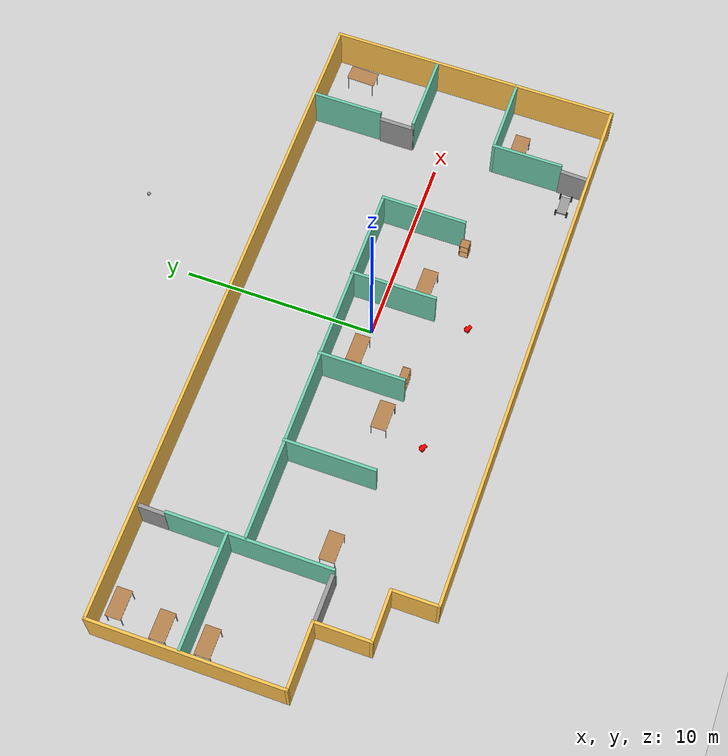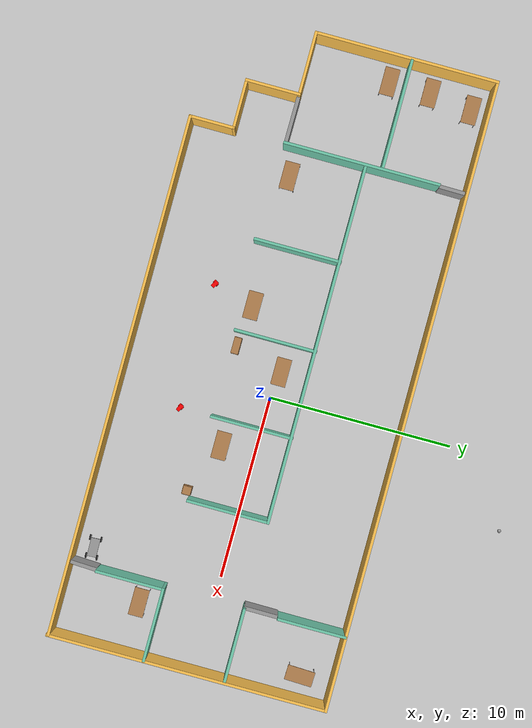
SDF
<sdf version="1.6">
 <world name="default">
  <plugin name="welcome_message" filename="libwelcome_message.so"/>
  <light name="sun" type="directional">
   <pose>0 0 10 0 -0 0</pose>
   <diffuse>0.8 0.8 0.8 1</diffuse>
   <specular>0.1 0.1 0.1 1</specular>
   <attenuation>
    <range>1000</range>
    <constant>0.9</constant>
    <linear>0.01</linear>
    <quadratic>0.001</quadratic>
   </attenuation>
   <direction>-0.5 0.5 -1</direction>
  </light>
  <model name="ground_plane">
   <static>1</static>
   <link name="link">
    <collision name="collision">
     <geometry><plane><normal>0 0 1</normal><size>100 100</size></plane></geometry>
     <surface><friction><ode><mu>100</mu><mu2>50</mu2></ode></friction></surface>
    </collision>
    <visual name="visual">
     <cast_shadows>0</cast_shadows>
     <geometry><plane><normal>0 0 1</normal><size>100 100</size></plane></geometry>
     <material>
      <script><uri>file://media/materials/scripts/gazebo.material</uri><name>Gazebo/Grey</name></script>
     </material>
    </visual>
   </link>
  </model>
  <gravity>0 0 -9.8</gravity>
  <magnetic_field>6e-06 2.3e-05 -4.2e-05</magnetic_field>
  <atmosphere type="adiabatic"/>
  <physics name="default_physics" default="0" type="ode">
   <max_step_size>0.001</max_step_size>
   <real_time_factor>1</real_time_factor>
   <real_time_update_rate>1000</real_time_update_rate>
  </physics>
  <scene><ambient>0.4 0.4 0.4 1</ambient><background>0.7 0.7 0.7 1</background><shadows>1</shadows></scene>
  <spherical_coordinates>
   <surface_model>EARTH_WGS84</surface_model>
   <latitude_deg>0</latitude_deg>
   <longitude_deg>0</longitude_deg>
   <elevation>0</elevation>
   <heading_deg>0</heading_deg>
  </spherical_coordinates>
  <model name="Building">
   <pose>-2.0428 -0.42646 0 0 -0 0</pose>
   <link name="Door_0">
    <collision name="Door_0_Collision">
     <geometry><box><size>2.58109 0.2 2</size></box></geometry>
     <pose>0 0 1 0 -0 0</pose>
    </collision>
    <visual name="Door_0_Visual">
     <pose>0 0 1 0 -0 0</pose>
     <geometry><box><size>2.58109 0.2 2</size></box></geometry>
     <material>
      <script><uri>file://media/materials/scripts/gazebo.material</uri><name>Gazebo/Grey</name></script>
     </material>
    </visual>
    <pose>-12.3535 -2.32405 0 0 -0 3.13435</pose>
   </link>
   <link name="Door_1">
    <collision name="Door_1_Collision">
     <geometry><box><size>1.8268 0.2 2</size></box></geometry>
     <pose>0 0 1 0 -0 0</pose>
    </collision>
    <visual name="Door_1_Visual">
     <pose>0 0 1 0 -0 0</pose>
     <geometry><box><size>1.8268 0.2 2</size></box></geometry>
     <material>
      <script><uri>file://media/materials/scripts/gazebo.material</uri><name>Gazebo/Grey</name></script>
     </material>
    </visual>
    <pose>13.0292 2.92693 0 0 -0 1.5655</pose>
   </link>
   <link name="Door_2">
    <collision name="Door_2_Collision">
     <geometry><box><size>1.47434 0.2 2</size></box></geometry>
     <pose>0 0 1 0 -0 0</pose>
    </collision>
    <visual name="Door_2_Visual">
     <pose>0 0 1 0 -0 0</pose>
     <geometry><box><size>1.47434 0.2 2</size></box></geometry>
     <material>
      <script><uri>file://media/materials/scripts/gazebo.material</uri><name>Gazebo/Grey</name></script>
     </material>
    </visual>
    <pose>13.1149 -6.73153 0 0 -0 1.52915</pose>
   </link>
   <link name="Door_3">
    <collision name="Door_3_Collision">
     <geometry><box><size>1.38773 0.2 2</size></box></geometry>
     <pose>0 0 1 0 -0 0</pose>
    </collision>
    <visual name="Door_3_Visual">
     <pose>0 0 1 0 -0 0</pose>
     <geometry><box><size>1.38773 0.2 2</size></box></geometry>
     <material>
      <script><uri>file://media/materials/scripts/gazebo.material</uri><name>Gazebo/Grey</name></script>
     </material>
    </visual>
    <pose>-11.0417 6.77121 0 0 0 -1.58178</pose>
   </link>
   <link name="Wall_0">
    <collision name="Wall_0_Collision">
     <geometry><box><size>28.25 0.15 2.5</size></box></geometry>
     <pose>0 0 1.25 0 -0 0</pose>
    </collision>
    <visual name="Wall_0_Visual">
     <pose>0 0 1.25 0 -0 0</pose>
     <geometry><box><size>28.25 0.15 2.5</size></box></geometry>
     <material>
      <script><uri>file://media/materials/scripts/gazebo.material</uri><name>Gazebo/Grey</name></script>
      <ambient>1 0.764706 0.305882 1</ambient>
     </material>
     <meta><layer>0</layer></meta>
    </visual>
    <pose>2.95 -7.5 0 0 -0 0</pose>
   </link>
   <link name="Wall_10">
    <collision name="Wall_10_Collision">
     <geometry><box><size>8.5 0.15 2.5</size></box></geometry>
     <pose>0 0 1.25 0 -0 0</pose>
    </collision>
    <visual name="Wall_10_Visual">
     <pose>0 0 1.25 0 -0 0</pose>
     <geometry><box><size>8.5 0.15 2.5</size></box></geometry>
     <material>
      <script><uri>file://media/materials/scripts/gazebo.material</uri><name>Gazebo/Grey</name></script>
      <ambient>0.435294 0.796078 0.67451 1</ambient>
     </material>
     <meta><layer>0</layer></meta>
    </visual>
    <pose>-11.0694 1.81529 0 0 0 -1.5708</pose>
   </link>
   <link name="Wall_12">
    <collision name="Wall_12_Collision">
     <geometry><box><size>6 0.15 2.5</size></box></geometry>
     <pose>0 0 1.25 0 -0 0</pose>
    </collision>
    <visual name="Wall_12_Visual">
     <pose>0 0 1.25 0 -0 0</pose>
     <geometry><box><size>6 0.15 2.5</size></box></geometry>
     <material>
      <script><uri>file://media/materials/scripts/gazebo.material</uri><name>Gazebo/Grey</name></script>
      <ambient>0.435294 0.796078 0.67451 1</ambient>
     </material>
     <meta><layer>0</layer></meta>
    </visual>
    <pose>-14.0177 2.93127 0 0 -0 0</pose>
   </link>
   <link name="Wall_14">
    <collision name="Wall_14_Collision">
     <geometry><box><size>19.5 0.15 2.5</size></box></geometry>
     <pose>0 0 1.25 0 -0 0</pose>
    </collision>
    <visual name="Wall_14_Visual">
     <pose>0 0 1.25 0 -0 0</pose>
     <geometry><box><size>19.5 0.15 2.5</size></box></geometry>
     <material>
      <script><uri>file://media/materials/scripts/gazebo.material</uri><name>Gazebo/Grey</name></script>
      <ambient>0.435294 0.796078 0.67451 1</ambient>
     </material>
     <meta><layer>0</layer></meta>
    </visual>
    <pose>-1.33323 2.04415 0 0 -0 0</pose>
   </link>
   <link name="Wall_15">
    <collision name="Wall_15_Collision">
     <geometry><box><size>4.5 0.15 2.5</size></box></geometry>
     <pose>0 0 1.25 0 -0 0</pose>
    </collision>
    <visual name="Wall_15_Visual">
     <pose>0 0 1.25 0 -0 0</pose>
     <geometry><box><size>4.5 0.15 2.5</size></box></geometry>
     <material>
      <script><uri>file://media/materials/scripts/gazebo.material</uri><name>Gazebo/Grey</name></script>
      <ambient>0.435294 0.796078 0.67451 1</ambient>
     </material>
     <meta><layer>0</layer></meta>
    </visual>
    <pose>8.34177 -0.130849 0 0 0 -1.5708</pose>
   </link>
   <link name="Wall_17">
    <collision name="Wall_17_Collision">
     <geometry><box><size>4.5 0.15 2.5</size></box></geometry>
     <pose>0 0 1.25 0 -0 0</pose>
    </collision>
    <visual name="Wall_17_Visual">
     <pose>0 0 1.25 0 -0 0</pose>
     <geometry><box><size>4.5 0.15 2.5</size></box></geometry>
     <material>
      <script><uri>file://media/materials/scripts/gazebo.material</uri><name>Gazebo/Grey</name></script>
      <ambient>0.435294 0.796078 0.67451 1</ambient>
     </material>
     <meta><layer>0</layer></meta>
    </visual>
    <pose>-0.944044 -0.100258 0 0 0 -1.5708</pose>
   </link>
   <link name="Wall_19">
    <collision name="Wall_19_Collision">
     <geometry><box><size>4.75 0.15 2.5</size></box></geometry>
     <pose>0 0 1.25 0 -0 0</pose>
    </collision>
    <visual name="Wall_19_Visual">
     <pose>0 0 1.25 0 -0 0</pose>
     <geometry><box><size>4.75 0.15 2.5</size></box></geometry>
     <material>
      <script><uri>file://media/materials/scripts/gazebo.material</uri><name>Gazebo/Grey</name></script>
      <ambient>0.435294 0.796078 0.67451 1</ambient>
     </material>
     <meta><layer>0</layer></meta>
    </visual>
    <pose>-5.80789 -0.225258 0 0 0 -1.5708</pose>
   </link>
   <link name="Wall_2">
    <collision name="Wall_2_Collision">
     <geometry><box><size>2.5 0.15 2.5</size></box></geometry>
     <pose>0 0 1.25 0 -0 0</pose>
    </collision>
    <visual name="Wall_2_Visual">
     <pose>0 0 1.25 0 -0 0</pose>
     <geometry><box><size>2.5 0.15 2.5</size></box></geometry>
     <material>
      <script><uri>file://media/materials/scripts/gazebo.material</uri><name>Gazebo/Grey</name></script>
      <ambient>1 0.764706 0.305882 1</ambient>
     </material>
     <meta><layer>0</layer></meta>
    </visual>
    <pose>-11.1 -6.325 0 0 -0 1.5708</pose>
   </link>
   <link name="Wall_21">
    <collision name="Wall_21_Collision">
     <geometry><box><size>4.5 0.15 2.5</size></box></geometry>
     <pose>0 0 1.25 0 -0 0</pose>
    </collision>
    <visual name="Wall_21_Visual">
     <pose>0 0 1.25 0 -0 0</pose>
     <geometry><box><size>4.5 0.15 2.5</size></box></geometry>
     <material>
      <script><uri>file://media/materials/scripts/gazebo.material</uri><name>Gazebo/Grey</name></script>
      <ambient>0.435294 0.796078 0.67451 1</ambient>
     </material>
     <meta><layer>0</layer></meta>
    </visual>
    <pose>3.76685 -0.100258 0 0 0 -1.5708</pose>
   </link>
   <link name="Wall_25">
    <collision name="Wall_25_Collision">
     <geometry><box><size>4 0.15 2.5</size></box></geometry>
     <pose>0 0 1.25 0 -0 0</pose>
    </collision>
    <visual name="Wall_25_Visual">
     <pose>0 0 1.25 0 -0 0</pose>
     <geometry><box><size>4 0.15 2.5</size></box></geometry>
     <material>
      <script><uri>file://media/materials/scripts/gazebo.material</uri><name>Gazebo/Grey</name></script>
      <ambient>0.435294 0.796078 0.67451 1</ambient>
     </material>
     <meta><layer>0</layer></meta>
    </visual>
    <pose>14.9913 2.04415 0 0 -0 0</pose>
   </link>
   <link name="Wall_27">
    <collision name="Wall_27_Collision">
     <geometry><box><size>4 0.15 2.5</size></box></geometry>
     <pose>0 0 1.25 0 -0 0</pose>
    </collision>
    <visual name="Wall_27_Visual">
     <pose>0 0 1.25 0 -0 0</pose>
     <geometry><box><size>4 0.15 2.5</size></box></geometry>
     <material>
      <script><uri>file://media/materials/scripts/gazebo.material</uri><name>Gazebo/Grey</name></script>
      <ambient>0.435294 0.796078 0.67451 1</ambient>
     </material>
     <meta><layer>0</layer></meta>
    </visual>
    <pose>15.0831 -2.33025 0 0 -0 0</pose>
   </link>
   <link name="Wall_29">
    <collision name="Wall_29_Collision">
     <geometry><box><size>3.75 0.15 2.5</size></box></geometry>
     <pose>0 0 1.25 0 -0 0</pose>
    </collision>
    <visual name="Wall_29_Visual">
     <pose>0 0 1.25 0 -0 0</pose>
     <geometry><box><size>3.75 0.15 2.5</size></box></geometry>
     <material>
      <script><uri>file://media/materials/scripts/gazebo.material</uri><name>Gazebo/Grey</name></script>
      <ambient>0.435294 0.796078 0.67451 1</ambient>
     </material>
     <meta><layer>0</layer></meta>
    </visual>
    <pose>13.1581 -4.13025 0 0 0 -1.5708</pose>
   </link>
   <link name="Wall_3">
    <collision name="Wall_3_Collision">
     <geometry><box><size>2.75 0.15 2.5</size></box></geometry>
     <pose>0 0 1.25 0 -0 0</pose>
    </collision>
    <visual name="Wall_3_Visual">
     <pose>0 0 1.25 0 -0 0</pose>
     <geometry><box><size>2.75 0.15 2.5</size></box></geometry>
     <material>
      <script><uri>file://media/materials/scripts/gazebo.material</uri><name>Gazebo/Grey</name></script>
      <ambient>1 0.764706 0.305882 1</ambient>
     </material>
     <meta><layer>0</layer></meta>
    </visual>
    <pose>-12.4 -5.15 0 0 -0 3.14159</pose>
   </link>
   <link name="Wall_31">
    <collision name="Wall_31_Collision">
     <geometry><box><size>3.75 0.15 2.5</size></box></geometry>
     <pose>0 0 1.25 0 -0 0</pose>
    </collision>
    <visual name="Wall_31_Visual">
     <pose>0 0 1.25 0 -0 0</pose>
     <geometry><box><size>3.75 0.15 2.5</size></box></geometry>
     <material>
      <script><uri>file://media/materials/scripts/gazebo.material</uri><name>Gazebo/Grey</name></script>
      <ambient>0.435294 0.796078 0.67451 1</ambient>
     </material>
     <meta><layer>0</layer></meta>
    </visual>
    <pose>13.0663 5.71016 0 0 -0 1.5708</pose>
   </link>
   <link name="Wall_4">
    <collision name="Wall_4_Collision">
     <geometry><box><size>3 0.15 2.5</size></box></geometry>
     <pose>0 0 1.25 0 -0 0</pose>
    </collision>
    <visual name="Wall_4_Visual">
     <pose>0 0 1.25 0 -0 0</pose>
     <geometry><box><size>3 0.15 2.5</size></box></geometry>
     <material>
      <script><uri>file://media/materials/scripts/gazebo.material</uri><name>Gazebo/Grey</name></script>
      <ambient>1 0.764706 0.305882 1</ambient>
     </material>
     <meta><layer>0</layer></meta>
    </visual>
    <pose>-13.7 -3.725 0 0 -0 1.5708</pose>
   </link>
   <link name="Wall_5">
    <collision name="Wall_5_Collision">
     <geometry><box><size>3.5 0.15 2.5</size></box></geometry>
     <pose>0 0 1.25 0 -0 0</pose>
    </collision>
    <visual name="Wall_5_Visual">
     <pose>0 0 1.25 0 -0 0</pose>
     <geometry><box><size>3.5 0.15 2.5</size></box></geometry>
     <material>
      <script><uri>file://media/materials/scripts/gazebo.material</uri><name>Gazebo/Grey</name></script>
      <ambient>1 0.764706 0.305882 1</ambient>
     </material>
     <meta><layer>0</layer></meta>
    </visual>
    <pose>-15.375 -2.3 0 0 -0 3.14159</pose>
   </link>
   <link name="Wall_6">
    <collision name="Wall_6_Collision">
     <geometry><box><size>10 0.15 2.5</size></box></geometry>
     <pose>0 0 1.25 0 -0 0</pose>
    </collision>
    <visual name="Wall_6_Visual">
     <pose>0 0 1.25 0 -0 0</pose>
     <geometry><box><size>10 0.15 2.5</size></box></geometry>
     <material>
      <script><uri>file://media/materials/scripts/gazebo.material</uri><name>Gazebo/Grey</name></script>
      <ambient>1 0.764706 0.305882 1</ambient>
     </material>
     <meta><layer>0</layer></meta>
    </visual>
    <pose>-17.05 2.625 0 0 -0 1.5708</pose>
   </link>
   <link name="Wall_7">
    <collision name="Wall_7_Collision">
     <geometry><box><size>34.25 0.15 2.5</size></box></geometry>
     <pose>0 0 1.25 0 -0 0</pose>
    </collision>
    <visual name="Wall_7_Visual">
     <pose>0 0 1.25 0 -0 0</pose>
     <geometry><box><size>34.25 0.15 2.5</size></box></geometry>
     <material>
      <script><uri>file://media/materials/scripts/gazebo.material</uri><name>Gazebo/Grey</name></script>
      <ambient>1 0.764706 0.305882 1</ambient>
     </material>
     <meta><layer>0</layer></meta>
    </visual>
    <pose>0 7.55 0 0 -0 0</pose>
   </link>
   <link name="Wall_8">
    <collision name="Wall_8_Collision">
     <geometry><box><size>15.25 0.15 2.5</size></box></geometry>
     <pose>0 0 1.25 0 -0 0</pose>
    </collision>
    <visual name="Wall_8_Visual">
     <pose>0 0 1.25 0 -0 0</pose>
     <geometry><box><size>15.25 0.15 2.5</size></box></geometry>
     <material>
      <script><uri>file://media/materials/scripts/gazebo.material</uri><name>Gazebo/Grey</name></script>
      <ambient>1 0.764706 0.305882 1</ambient>
     </material>
     <meta><layer>0</layer></meta>
    </visual>
    <pose>17.05 0 0 0 0 -1.5708</pose>
   </link>
   <static>1</static>
  </model>
  <model name="HumanoidRobot">
   <link name="link_0">
    <pose>-0.053333 0.003341 0 0 -0 0</pose>
    <inertial>
     <mass>1</mass>
     <inertia>
      <ixx>0.166667</ixx>
      <ixy>0</ixy>
      <ixz>0</ixz>
      <iyy>0.166667</iyy>
      <iyz>0</iyz>
      <izz>0.166667</izz>
     </inertia>
    </inertial>
    <visual name="ModelPreview_0::link_0::visual_1">
     <pose>-0.15 0 -0.05 0 -0 0</pose>
     <geometry><sphere><radius>0.05</radius></sphere></geometry>
     <material>
      <lighting>1</lighting>
      <script><uri>file://media/materials/scripts/gazebo.material</uri><name>Gazebo/Grey</name></script>
      <shader type="pixel"><normal_map>__default__</normal_map></shader>
      <ambient>1 0 0 1</ambient>
      <diffuse>1 0 0 1</diffuse>
      <specular>1 0 0 1</specular>
      <emissive>0 0 0 1</emissive>
     </material>
    </visual>
    <visual name="visual">
     <geometry><box><size>0.4 0.2 0.1</size></box></geometry>
     <material>
      <lighting>1</lighting>
      <script><uri>file://media/materials/scripts/gazebo.material</uri><name>Gazebo/Grey</name></script>
      <shader type="pixel"><normal_map>__default__</normal_map></shader>
      <ambient>1 0 0 1</ambient>
      <diffuse>1 0 0 1</diffuse>
      <specular>1 0 0 1</specular>
      <emissive>0 0 0 1</emissive>
     </material>
    </visual>
    <collision name="collision_1">
     <pose>-0.15 0 -0.05 0 -0 0</pose>
     <geometry><sphere><radius>0.05</radius></sphere></geometry>
     <surface>
      <friction>
       <ode><mu>0</mu><mu2>0</mu2><fdir1>0 0 0</fdir1><slip1>1</slip1><slip2>1</slip2></ode>
       <torsional>
        <coefficient>1</coefficient>
        <patch_radius>0</patch_radius>
        <surface_radius>0</surface_radius>
        <use_patch_radius>1</use_patch_radius>
        <ode><slip>0</slip></ode>
       </torsional>
      </friction>
      <bounce><restitution_coefficient>0</restitution_coefficient><threshold>1e+06</threshold></bounce>
      <contact>
       <collide_without_contact>0</collide_without_contact>
       <collide_without_contact_bitmask>1</collide_without_contact_bitmask>
       <collide_bitmask>1</collide_bitmask>
       <ode>
        <soft_cfm>0</soft_cfm>
        <soft_erp>0.2</soft_erp>
        <kp>1e+13</kp>
        <kd>1</kd>
        <max_vel>0.01</max_vel>
        <min_depth>0</min_depth>
       </ode>
       <bullet>
        <split_impulse>1</split_impulse>
        <split_impulse_penetration_threshold>-0.01</split_impulse_penetration_threshold>
        <soft_cfm>0</soft_cfm>
        <soft_erp>0.2</soft_erp>
        <kp>1e+13</kp>
        <kd>1</kd>
       </bullet>
      </contact>
     </surface>
    </collision>
    <collision name="collision">
     <geometry><box><size>0.4 0.2 0.1</size></box></geometry>
     <surface>
      <friction>
       <ode><mu>1</mu><mu2>1</mu2><fdir1>0 0 0</fdir1><slip1>0</slip1><slip2>0</slip2></ode>
       <torsional>
        <coefficient>1</coefficient>
        <patch_radius>0</patch_radius>
        <surface_radius>0</surface_radius>
        <use_patch_radius>1</use_patch_radius>
        <ode><slip>0</slip></ode>
       </torsional>
      </friction>
      <bounce><restitution_coefficient>0</restitution_coefficient><threshold>1e+06</threshold></bounce>
      <contact>
       <collide_without_contact>0</collide_without_contact>
       <collide_without_contact_bitmask>1</collide_without_contact_bitmask>
       <collide_bitmask>1</collide_bitmask>
       <ode>
        <soft_cfm>0</soft_cfm>
        <soft_erp>0.2</soft_erp>
        <kp>1e+13</kp>
        <kd>1</kd>
        <max_vel>0.01</max_vel>
        <min_depth>0</min_depth>
       </ode>
       <bullet>
        <split_impulse>1</split_impulse>
        <split_impulse_penetration_threshold>-0.01</split_impulse_penetration_threshold>
        <soft_cfm>0</soft_cfm>
        <soft_erp>0.2</soft_erp>
        <kp>1e+13</kp>
        <kd>1</kd>
       </bullet>
      </contact>
     </surface>
    </collision>
   </link>
   <link name="link_1">
    <pose>0.006667 -0.121672 0 1.5707 -0 0</pose>
    <inertial>
     <mass>1</mass>
     <inertia><ixx>0.145833</ixx><ixy>0</ixy><ixz>0</ixz><iyy>0.145833</iyy><iyz>0</iyz><izz>0.125</izz></inertia>
    </inertial>
    <visual name="visual">
     <geometry><cylinder><radius>0.1</radius><length>0.05</length></cylinder></geometry>
     <material>
      <lighting>1</lighting>
      <script><uri>file://media/materials/scripts/gazebo.material</uri><name>Gazebo/Grey</name></script>
      <shader type="pixel"><normal_map>__default__</normal_map></shader>
      <ambient>1 0 0 1</ambient>
      <diffuse>1 0 0 1</diffuse>
      <specular>1 0 0 1</specular>
      <emissive>0 0 0 1</emissive>
     </material>
    </visual>
    <collision name="collision">
     <geometry><cylinder><radius>0.1</radius><length>0.05</length></cylinder></geometry>
     <surface>
      <friction>
       <ode><mu>1</mu><mu2>1</mu2><fdir1>0 0 0</fdir1><slip1>0</slip1><slip2>0</slip2></ode>
       <torsional>
        <coefficient>1</coefficient>
        <patch_radius>0</patch_radius>
        <surface_radius>0</surface_radius>
        <use_patch_radius>1</use_patch_radius>
        <ode><slip>0</slip></ode>
       </torsional>
      </friction>
      <bounce><restitution_coefficient>0</restitution_coefficient><threshold>1e+06</threshold></bounce>
      <contact>
       <collide_without_contact>0</collide_without_contact>
       <collide_without_contact_bitmask>1</collide_without_contact_bitmask>
       <collide_bitmask>1</collide_bitmask>
       <ode>
        <soft_cfm>0</soft_cfm>
        <soft_erp>0.2</soft_erp>
        <kp>1e+13</kp>
        <kd>1</kd>
        <max_vel>0.01</max_vel>
        <min_depth>0</min_depth>
       </ode>
       <bullet>
        <split_impulse>1</split_impulse>
        <split_impulse_penetration_threshold>-0.01</split_impulse_penetration_threshold>
        <soft_cfm>0</soft_cfm>
        <soft_erp>0.2</soft_erp>
        <kp>1e+13</kp>
        <kd>1</kd>
       </bullet>
      </contact>
     </surface>
    </collision>
   </link>
   <link name="link_1_clone">
    <pose>0.046667 0.118331 0 1.5707 -0 0</pose>
    <inertial>
     <mass>1</mass>
     <inertia><ixx>0.145833</ixx><ixy>0</ixy><ixz>0</ixz><iyy>0.145833</iyy><iyz>0</iyz><izz>0.125</izz></inertia>
    </inertial>
    <visual name="visual">
     <geometry><cylinder><radius>0.1</radius><length>0.05</length></cylinder></geometry>
     <material>
      <lighting>1</lighting>
      <script><uri>file://media/materials/scripts/gazebo.material</uri><name>Gazebo/Grey</name></script>
      <shader type="pixel"><normal_map>__default__</normal_map></shader>
      <ambient>1 0 0 1</ambient>
      <diffuse>1 0 0 1</diffuse>
      <specular>1 0 0 1</specular>
      <emissive>0 0 0 1</emissive>
     </material>
    </visual>
    <collision name="collision">
     <geometry><cylinder><radius>0.1</radius><length>0.05</length></cylinder></geometry>
     <surface>
      <friction>
       <ode><mu>1</mu><mu2>1</mu2><fdir1>0 0 0</fdir1><slip1>0</slip1><slip2>0</slip2></ode>
       <torsional>
        <coefficient>1</coefficient>
        <patch_radius>0</patch_radius>
        <surface_radius>0</surface_radius>
        <use_patch_radius>1</use_patch_radius>
        <ode><slip>0</slip></ode>
       </torsional>
      </friction>
      <bounce><restitution_coefficient>0</restitution_coefficient><threshold>1e+06</threshold></bounce>
      <contact>
       <collide_without_contact>0</collide_without_contact>
       <collide_without_contact_bitmask>1</collide_without_contact_bitmask>
       <collide_bitmask>1</collide_bitmask>
       <ode>
        <soft_cfm>0</soft_cfm>
        <soft_erp>0.2</soft_erp>
        <kp>1e+13</kp>
        <kd>1</kd>
        <max_vel>0.01</max_vel>
        <min_depth>0</min_depth>
       </ode>
       <bullet>
        <split_impulse>1</split_impulse>
        <split_impulse_penetration_threshold>-0.01</split_impulse_penetration_threshold>
        <soft_cfm>0</soft_cfm>
        <soft_erp>0.2</soft_erp>
        <kp>1e+13</kp>
        <kd>1</kd>
       </bullet>
      </contact>
     </surface>
    </collision>
   </link>
   <joint name="link_0_JOINT_0" type="revolute">
    <parent>link_0</parent>
    <child>link_1</child>
    <axis>
     <xyz>0 0 1</xyz>
     <use_parent_model_frame>0</use_parent_model_frame>
     <limit>
      <lower>-1.79769e+308</lower>
      <upper>1.79769e+308</upper>
      <effort>-1</effort>
      <velocity>-1</velocity>
     </limit>
     <dynamics>
      <spring_reference>0</spring_reference>
      <spring_stiffness>0</spring_stiffness>
      <damping>0</damping>
     </dynamics>
    </axis>
    <physics>
     <ode><limit><cfm>0</cfm><erp>0.2</erp></limit><suspension><cfm>0</cfm><erp>0.2</erp></suspension></ode>
    </physics>
   </joint>
   <joint name="link_0_JOINT_1" type="revolute">
    <parent>link_0</parent>
    <child>link_1_clone</child>
    <axis>
     <xyz>0 0 1</xyz>
     <use_parent_model_frame>0</use_parent_model_frame>
     <limit>
      <lower>-1.79769e+308</lower>
      <upper>1.79769e+308</upper>
      <effort>-1</effort>
      <velocity>-1</velocity>
     </limit>
     <dynamics>
      <spring_reference>0</spring_reference>
      <spring_stiffness>0</spring_stiffness>
      <damping>0</damping>
     </dynamics>
    </axis>
    <physics>
     <ode><limit><cfm>0</cfm><erp>0.2</erp></limit><suspension><cfm>0</cfm><erp>0.2</erp></suspension></ode>
    </physics>
   </joint>
   <static>0</static>
   <pose>-5.15019 -4.44642 0.099998 -1.3e-05 1.2e-05 2.62297</pose>
  </model>
  <model name="HumanoidRobot_0">
   <link name="link_0">
    <pose>-0.053333 0.003341 0 0 -0 0</pose>
    <inertial>
     <mass>1</mass>
     <inertia>
      <ixx>0.166667</ixx>
      <ixy>0</ixy>
      <ixz>0</ixz>
      <iyy>0.166667</iyy>
      <iyz>0</iyz>
      <izz>0.166667</izz>
     </inertia>
    </inertial>
    <visual name="ModelPreview_0::link_0::visual_1">
     <pose>-0.15 0 -0.05 0 -0 0</pose>
     <geometry><sphere><radius>0.05</radius></sphere></geometry>
     <material>
      <lighting>1</lighting>
      <script><uri>file://media/materials/scripts/gazebo.material</uri><name>Gazebo/Grey</name></script>
      <shader type="pixel"><normal_map>__default__</normal_map></shader>
      <ambient>1 0 0 1</ambient>
      <diffuse>1 0 0 1</diffuse>
      <specular>1 0 0 1</specular>
      <emissive>0 0 0 1</emissive>
     </material>
    </visual>
    <visual name="visual">
     <geometry><box><size>0.4 0.2 0.1</size></box></geometry>
     <material>
      <lighting>1</lighting>
      <script><uri>file://media/materials/scripts/gazebo.material</uri><name>Gazebo/Grey</name></script>
      <shader type="pixel"><normal_map>__default__</normal_map></shader>
      <ambient>1 0 0 1</ambient>
      <diffuse>1 0 0 1</diffuse>
      <specular>1 0 0 1</specular>
      <emissive>0 0 0 1</emissive>
     </material>
    </visual>
    <collision name="collision_1">
     <pose>-0.15 0 -0.05 0 -0 0</pose>
     <geometry><sphere><radius>0.05</radius></sphere></geometry>
     <surface>
      <friction>
       <ode><mu>0</mu><mu2>0</mu2><fdir1>0 0 0</fdir1><slip1>1</slip1><slip2>1</slip2></ode>
       <torsional>
        <coefficient>1</coefficient>
        <patch_radius>0</patch_radius>
        <surface_radius>0</surface_radius>
        <use_patch_radius>1</use_patch_radius>
        <ode><slip>0</slip></ode>
       </torsional>
      </friction>
      <bounce><restitution_coefficient>0</restitution_coefficient><threshold>1e+06</threshold></bounce>
      <contact>
       <collide_without_contact>0</collide_without_contact>
       <collide_without_contact_bitmask>1</collide_without_contact_bitmask>
       <collide_bitmask>1</collide_bitmask>
       <ode>
        <soft_cfm>0</soft_cfm>
        <soft_erp>0.2</soft_erp>
        <kp>1e+13</kp>
        <kd>1</kd>
        <max_vel>0.01</max_vel>
        <min_depth>0</min_depth>
       </ode>
       <bullet>
        <split_impulse>1</split_impulse>
        <split_impulse_penetration_threshold>-0.01</split_impulse_penetration_threshold>
        <soft_cfm>0</soft_cfm>
        <soft_erp>0.2</soft_erp>
        <kp>1e+13</kp>
        <kd>1</kd>
       </bullet>
      </contact>
     </surface>
    </collision>
    <collision name="collision">
     <geometry><box><size>0.4 0.2 0.1</size></box></geometry>
     <surface>
      <friction>
       <ode><mu>1</mu><mu2>1</mu2><fdir1>0 0 0</fdir1><slip1>0</slip1><slip2>0</slip2></ode>
       <torsional>
        <coefficient>1</coefficient>
        <patch_radius>0</patch_radius>
        <surface_radius>0</surface_radius>
        <use_patch_radius>1</use_patch_radius>
        <ode><slip>0</slip></ode>
       </torsional>
      </friction>
      <bounce><restitution_coefficient>0</restitution_coefficient><threshold>1e+06</threshold></bounce>
      <contact>
       <collide_without_contact>0</collide_without_contact>
       <collide_without_contact_bitmask>1</collide_without_contact_bitmask>
       <collide_bitmask>1</collide_bitmask>
       <ode>
        <soft_cfm>0</soft_cfm>
        <soft_erp>0.2</soft_erp>
        <kp>1e+13</kp>
        <kd>1</kd>
        <max_vel>0.01</max_vel>
        <min_depth>0</min_depth>
       </ode>
       <bullet>
        <split_impulse>1</split_impulse>
        <split_impulse_penetration_threshold>-0.01</split_impulse_penetration_threshold>
        <soft_cfm>0</soft_cfm>
        <soft_erp>0.2</soft_erp>
        <kp>1e+13</kp>
        <kd>1</kd>
       </bullet>
      </contact>
     </surface>
    </collision>
   </link>
   <link name="link_1">
    <pose>0.006667 -0.121672 0 1.5707 -0 0</pose>
    <inertial>
     <mass>1</mass>
     <inertia><ixx>0.145833</ixx><ixy>0</ixy><ixz>0</ixz><iyy>0.145833</iyy><iyz>0</iyz><izz>0.125</izz></inertia>
    </inertial>
    <visual name="visual">
     <geometry><cylinder><radius>0.1</radius><length>0.05</length></cylinder></geometry>
     <material>
      <lighting>1</lighting>
      <script><uri>file://media/materials/scripts/gazebo.material</uri><name>Gazebo/Grey</name></script>
      <shader type="pixel"><normal_map>__default__</normal_map></shader>
      <ambient>1 0 0 1</ambient>
      <diffuse>1 0 0 1</diffuse>
      <specular>1 0 0 1</specular>
      <emissive>0 0 0 1</emissive>
     </material>
    </visual>
    <collision name="collision">
     <geometry><cylinder><radius>0.1</radius><length>0.05</length></cylinder></geometry>
     <surface>
      <friction>
       <ode><mu>1</mu><mu2>1</mu2><fdir1>0 0 0</fdir1><slip1>0</slip1><slip2>0</slip2></ode>
       <torsional>
        <coefficient>1</coefficient>
        <patch_radius>0</patch_radius>
        <surface_radius>0</surface_radius>
        <use_patch_radius>1</use_patch_radius>
        <ode><slip>0</slip></ode>
       </torsional>
      </friction>
      <bounce><restitution_coefficient>0</restitution_coefficient><threshold>1e+06</threshold></bounce>
      <contact>
       <collide_without_contact>0</collide_without_contact>
       <collide_without_contact_bitmask>1</collide_without_contact_bitmask>
       <collide_bitmask>1</collide_bitmask>
       <ode>
        <soft_cfm>0</soft_cfm>
        <soft_erp>0.2</soft_erp>
        <kp>1e+13</kp>
        <kd>1</kd>
        <max_vel>0.01</max_vel>
        <min_depth>0</min_depth>
       </ode>
       <bullet>
        <split_impulse>1</split_impulse>
        <split_impulse_penetration_threshold>-0.01</split_impulse_penetration_threshold>
        <soft_cfm>0</soft_cfm>
        <soft_erp>0.2</soft_erp>
        <kp>1e+13</kp>
        <kd>1</kd>
       </bullet>
      </contact>
     </surface>
    </collision>
   </link>
   <link name="link_1_clone">
    <pose>0.046667 0.118331 0 1.5707 -0 0</pose>
    <inertial>
     <mass>1</mass>
     <inertia><ixx>0.145833</ixx><ixy>0</ixy><ixz>0</ixz><iyy>0.145833</iyy><iyz>0</iyz><izz>0.125</izz></inertia>
    </inertial>
    <visual name="visual">
     <geometry><cylinder><radius>0.1</radius><length>0.05</length></cylinder></geometry>
     <material>
      <lighting>1</lighting>
      <script><uri>file://media/materials/scripts/gazebo.material</uri><name>Gazebo/Grey</name></script>
      <shader type="pixel"><normal_map>__default__</normal_map></shader>
      <ambient>1 0 0 1</ambient>
      <diffuse>1 0 0 1</diffuse>
      <specular>1 0 0 1</specular>
      <emissive>0 0 0 1</emissive>
     </material>
    </visual>
    <collision name="collision">
     <geometry><cylinder><radius>0.1</radius><length>0.05</length></cylinder></geometry>
     <surface>
      <friction>
       <ode><mu>1</mu><mu2>1</mu2><fdir1>0 0 0</fdir1><slip1>0</slip1><slip2>0</slip2></ode>
       <torsional>
        <coefficient>1</coefficient>
        <patch_radius>0</patch_radius>
        <surface_radius>0</surface_radius>
        <use_patch_radius>1</use_patch_radius>
        <ode><slip>0</slip></ode>
       </torsional>
      </friction>
      <bounce><restitution_coefficient>0</restitution_coefficient><threshold>1e+06</threshold></bounce>
      <contact>
       <collide_without_contact>0</collide_without_contact>
       <collide_without_contact_bitmask>1</collide_without_contact_bitmask>
       <collide_bitmask>1</collide_bitmask>
       <ode>
        <soft_cfm>0</soft_cfm>
        <soft_erp>0.2</soft_erp>
        <kp>1e+13</kp>
        <kd>1</kd>
        <max_vel>0.01</max_vel>
        <min_depth>0</min_depth>
       </ode>
       <bullet>
        <split_impulse>1</split_impulse>
        <split_impulse_penetration_threshold>-0.01</split_impulse_penetration_threshold>
        <soft_cfm>0</soft_cfm>
        <soft_erp>0.2</soft_erp>
        <kp>1e+13</kp>
        <kd>1</kd>
       </bullet>
      </contact>
     </surface>
    </collision>
   </link>
   <joint name="link_0_JOINT_0" type="revolute">
    <parent>link_0</parent>
    <child>link_1</child>
    <axis>
     <xyz>0 0 1</xyz>
     <use_parent_model_frame>0</use_parent_model_frame>
     <limit>
      <lower>-1.79769e+308</lower>
      <upper>1.79769e+308</upper>
      <effort>-1</effort>
      <velocity>-1</velocity>
     </limit>
     <dynamics>
      <spring_reference>0</spring_reference>
      <spring_stiffness>0</spring_stiffness>
      <damping>0</damping>
     </dynamics>
    </axis>
    <physics>
     <ode><limit><cfm>0</cfm><erp>0.2</erp></limit><suspension><cfm>0</cfm><erp>0.2</erp></suspension></ode>
    </physics>
   </joint>
   <joint name="link_0_JOINT_1" type="revolute">
    <parent>link_0</parent>
    <child>link_1_clone</child>
    <axis>
     <xyz>0 0 1</xyz>
     <use_parent_model_frame>0</use_parent_model_frame>
     <limit>
      <lower>-1.79769e+308</lower>
      <upper>1.79769e+308</upper>
      <effort>-1</effort>
      <velocity>-1</velocity>
     </limit>
     <dynamics>
      <spring_reference>0</spring_reference>
      <spring_stiffness>0</spring_stiffness>
      <damping>0</damping>
     </dynamics>
    </axis>
    <physics>
     <ode><limit><cfm>0</cfm><erp>0.2</erp></limit><suspension><cfm>0</cfm><erp>0.2</erp></suspension></ode>
    </physics>
   </joint>
   <static>0</static>
   <pose>1.74661 -4.51152 0.100002 -1e-06 -1.1e-05 2.6717</pose>
  </model>
  <model name="table">
   <static>1</static>
   <link name="link">
    <collision name="surface">
     <pose>0 0 1 0 -0 0</pose>
     <geometry><box><size>1.5 0.8 0.03</size></box></geometry>
     <surface><friction><ode><mu>0.6</mu><mu2>0.6</mu2></ode></friction></surface>
    </collision>
    <visual name="visual1">
     <pose>0 0 1 0 -0 0</pose>
     <geometry><box><size>1.5 0.8 0.03</size></box></geometry>
     <material>
      <script><uri>file://media/materials/scripts/gazebo.material</uri><name>Gazebo/Wood</name></script>
     </material>
    </visual>
    <collision name="front_left_leg">
     <pose>0.68 0.38 0.5 0 -0 0</pose>
     <geometry><cylinder><radius>0.02</radius><length>1</length></cylinder></geometry>
    </collision>
    <visual name="front_left_leg">
     <pose>0.68 0.38 0.5 0 -0 0</pose>
     <geometry><cylinder><radius>0.02</radius><length>1</length></cylinder></geometry>
     <material>
      <script><uri>file://media/materials/scripts/gazebo.material</uri><name>Gazebo/Grey</name></script>
     </material>
    </visual>
    <collision name="front_right_leg">
     <pose>0.68 -0.38 0.5 0 -0 0</pose>
     <geometry><cylinder><radius>0.02</radius><length>1</length></cylinder></geometry>
    </collision>
    <visual name="front_right_leg">
     <pose>0.68 -0.38 0.5 0 -0 0</pose>
     <geometry><cylinder><radius>0.02</radius><length>1</length></cylinder></geometry>
     <material>
      <script><uri>file://media/materials/scripts/gazebo.material</uri><name>Gazebo/Grey</name></script>
     </material>
    </visual>
    <collision name="back_right_leg">
     <pose>-0.68 -0.38 0.5 0 -0 0</pose>
     <geometry><cylinder><radius>0.02</radius><length>1</length></cylinder></geometry>
    </collision>
    <visual name="back_right_leg">
     <pose>-0.68 -0.38 0.5 0 -0 0</pose>
     <geometry><cylinder><radius>0.02</radius><length>1</length></cylinder></geometry>
     <material>
      <script><uri>file://media/materials/scripts/gazebo.material</uri><name>Gazebo/Grey</name></script>
     </material>
    </visual>
    <collision name="back_left_leg">
     <pose>-0.68 0.38 0.5 0 -0 0</pose>
     <geometry><cylinder><radius>0.02</radius><length>1</length></cylinder></geometry>
    </collision>
    <visual name="back_left_leg">
     <pose>-0.68 0.38 0.5 0 -0 0</pose>
     <geometry><cylinder><radius>0.02</radius><length>1</length></cylinder></geometry>
     <material>
      <script><uri>file://media/materials/scripts/gazebo.material</uri><name>Gazebo/Grey</name></script>
     </material>
    </visual>
   </link>
   <pose>12.3187 -3.86475 0 0 -0 0</pose>
  </model>
  <model name="table_clone">
   <static>1</static>
   <link name="link">
    <collision name="surface">
     <pose>0 0 1 0 -0 0</pose>
     <geometry><box><size>1.5 0.8 0.03</size></box></geometry>
     <surface><friction><ode><mu>0.6</mu><mu2>0.6</mu2></ode></friction></surface>
    </collision>
    <visual name="visual1">
     <pose>0 0 1 0 -0 0</pose>
     <geometry><box><size>1.5 0.8 0.03</size></box></geometry>
     <material>
      <script><uri>file://media/materials/scripts/gazebo.material</uri><name>Gazebo/Wood</name></script>
     </material>
    </visual>
    <collision name="front_left_leg">
     <pose>0.68 0.38 0.5 0 -0 0</pose>
     <geometry><cylinder><radius>0.02</radius><length>1</length></cylinder></geometry>
    </collision>
    <visual name="front_left_leg">
     <pose>0.68 0.38 0.5 0 -0 0</pose>
     <geometry><cylinder><radius>0.02</radius><length>1</length></cylinder></geometry>
     <material>
      <script><uri>file://media/materials/scripts/gazebo.material</uri><name>Gazebo/Grey</name></script>
     </material>
    </visual>
    <collision name="front_right_leg">
     <pose>0.68 -0.38 0.5 0 -0 0</pose>
     <geometry><cylinder><radius>0.02</radius><length>1</length></cylinder></geometry>
    </collision>
    <visual name="front_right_leg">
     <pose>0.68 -0.38 0.5 0 -0 0</pose>
     <geometry><cylinder><radius>0.02</radius><length>1</length></cylinder></geometry>
     <material>
      <script><uri>file://media/materials/scripts/gazebo.material</uri><name>Gazebo/Grey</name></script>
     </material>
    </visual>
    <collision name="back_right_leg">
     <pose>-0.68 -0.38 0.5 0 -0 0</pose>
     <geometry><cylinder><radius>0.02</radius><length>1</length></cylinder></geometry>
    </collision>
    <visual name="back_right_leg">
     <pose>-0.68 -0.38 0.5 0 -0 0</pose>
     <geometry><cylinder><radius>0.02</radius><length>1</length></cylinder></geometry>
     <material>
      <script><uri>file://media/materials/scripts/gazebo.material</uri><name>Gazebo/Grey</name></script>
     </material>
    </visual>
    <collision name="back_left_leg">
     <pose>-0.68 0.38 0.5 0 -0 0</pose>
     <geometry><cylinder><radius>0.02</radius><length>1</length></cylinder></geometry>
    </collision>
    <visual name="back_left_leg">
     <pose>-0.68 0.38 0.5 0 -0 0</pose>
     <geometry><cylinder><radius>0.02</radius><length>1</length></cylinder></geometry>
     <material>
      <script><uri>file://media/materials/scripts/gazebo.material</uri><name>Gazebo/Grey</name></script>
     </material>
    </visual>
   </link>
   <pose>3.12494 -1.83773 0 0 -0 0</pose>
  </model>
  <model name="table_clone_0">
   <static>1</static>
   <link name="link">
    <collision name="surface">
     <pose>0 0 1 0 -0 0</pose>
     <geometry><box><size>1.5 0.8 0.03</size></box></geometry>
     <surface><friction><ode><mu>0.6</mu><mu2>0.6</mu2></ode></friction></surface>
    </collision>
    <visual name="visual1">
     <pose>0 0 1 0 -0 0</pose>
     <geometry><box><size>1.5 0.8 0.03</size></box></geometry>
     <material>
      <script><uri>file://media/materials/scripts/gazebo.material</uri><name>Gazebo/Wood</name></script>
     </material>
    </visual>
    <collision name="front_left_leg">
     <pose>0.68 0.38 0.5 0 -0 0</pose>
     <geometry><cylinder><radius>0.02</radius><length>1</length></cylinder></geometry>
    </collision>
    <visual name="front_left_leg">
     <pose>0.68 0.38 0.5 0 -0 0</pose>
     <geometry><cylinder><radius>0.02</radius><length>1</length></cylinder></geometry>
     <material>
      <script><uri>file://media/materials/scripts/gazebo.material</uri><name>Gazebo/Grey</name></script>
     </material>
    </visual>
    <collision name="front_right_leg">
     <pose>0.68 -0.38 0.5 0 -0 0</pose>
     <geometry><cylinder><radius>0.02</radius><length>1</length></cylinder></geometry>
    </collision>
    <visual name="front_right_leg">
     <pose>0.68 -0.38 0.5 0 -0 0</pose>
     <geometry><cylinder><radius>0.02</radius><length>1</length></cylinder></geometry>
     <material>
      <script><uri>file://media/materials/scripts/gazebo.material</uri><name>Gazebo/Grey</name></script>
     </material>
    </visual>
    <collision name="back_right_leg">
     <pose>-0.68 -0.38 0.5 0 -0 0</pose>
     <geometry><cylinder><radius>0.02</radius><length>1</length></cylinder></geometry>
    </collision>
    <visual name="back_right_leg">
     <pose>-0.68 -0.38 0.5 0 -0 0</pose>
     <geometry><cylinder><radius>0.02</radius><length>1</length></cylinder></geometry>
     <material>
      <script><uri>file://media/materials/scripts/gazebo.material</uri><name>Gazebo/Grey</name></script>
     </material>
    </visual>
    <collision name="back_left_leg">
     <pose>-0.68 0.38 0.5 0 -0 0</pose>
     <geometry><cylinder><radius>0.02</radius><length>1</length></cylinder></geometry>
    </collision>
    <visual name="back_left_leg">
     <pose>-0.68 0.38 0.5 0 -0 0</pose>
     <geometry><cylinder><radius>0.02</radius><length>1</length></cylinder></geometry>
     <material>
      <script><uri>file://media/materials/scripts/gazebo.material</uri><name>Gazebo/Grey</name></script>
     </material>
    </visual>
   </link>
   <pose>-1.48723 0.201904 0 0 -0 0</pose>
  </model>
  <model name="table_clone_clone">
   <static>1</static>
   <link name="link">
    <collision name="surface">
     <pose>0 0 1 0 -0 0</pose>
     <geometry><box><size>1.5 0.8 0.03</size></box></geometry>
     <surface><friction><ode><mu>0.6</mu><mu2>0.6</mu2></ode></friction></surface>
    </collision>
    <visual name="visual1">
     <pose>0 0 1 0 -0 0</pose>
     <geometry><box><size>1.5 0.8 0.03</size></box></geometry>
     <material>
      <script><uri>file://media/materials/scripts/gazebo.material</uri><name>Gazebo/Wood</name></script>
     </material>
    </visual>
    <collision name="front_left_leg">
     <pose>0.68 0.38 0.5 0 -0 0</pose>
     <geometry><cylinder><radius>0.02</radius><length>1</length></cylinder></geometry>
    </collision>
    <visual name="front_left_leg">
     <pose>0.68 0.38 0.5 0 -0 0</pose>
     <geometry><cylinder><radius>0.02</radius><length>1</length></cylinder></geometry>
     <material>
      <script><uri>file://media/materials/scripts/gazebo.material</uri><name>Gazebo/Grey</name></script>
     </material>
    </visual>
    <collision name="front_right_leg">
     <pose>0.68 -0.38 0.5 0 -0 0</pose>
     <geometry><cylinder><radius>0.02</radius><length>1</length></cylinder></geometry>
    </collision>
    <visual name="front_right_leg">
     <pose>0.68 -0.38 0.5 0 -0 0</pose>
     <geometry><cylinder><radius>0.02</radius><length>1</length></cylinder></geometry>
     <material>
      <script><uri>file://media/materials/scripts/gazebo.material</uri><name>Gazebo/Grey</name></script>
     </material>
    </visual>
    <collision name="back_right_leg">
     <pose>-0.68 -0.38 0.5 0 -0 0</pose>
     <geometry><cylinder><radius>0.02</radius><length>1</length></cylinder></geometry>
    </collision>
    <visual name="back_right_leg">
     <pose>-0.68 -0.38 0.5 0 -0 0</pose>
     <geometry><cylinder><radius>0.02</radius><length>1</length></cylinder></geometry>
     <material>
      <script><uri>file://media/materials/scripts/gazebo.material</uri><name>Gazebo/Grey</name></script>
     </material>
    </visual>
    <collision name="back_left_leg">
     <pose>-0.68 0.38 0.5 0 -0 0</pose>
     <geometry><cylinder><radius>0.02</radius><length>1</length></cylinder></geometry>
    </collision>
    <visual name="back_left_leg">
     <pose>-0.68 0.38 0.5 0 -0 0</pose>
     <geometry><cylinder><radius>0.02</radius><length>1</length></cylinder></geometry>
     <material>
      <script><uri>file://media/materials/scripts/gazebo.material</uri><name>Gazebo/Grey</name></script>
     </material>
    </visual>
   </link>
   <pose>-4.50263 -2.177 0 0 -0 0</pose>
  </model>
  <model name="table_clone_clone_0">
   <static>1</static>
   <link name="link">
    <collision name="surface">
     <pose>0 0 1 0 -0 0</pose>
     <geometry><box><size>1.5 0.8 0.03</size></box></geometry>
     <surface><friction><ode><mu>0.6</mu><mu2>0.6</mu2></ode></friction></surface>
    </collision>
    <visual name="visual1">
     <pose>0 0 1 0 -0 0</pose>
     <geometry><box><size>1.5 0.8 0.03</size></box></geometry>
     <material>
      <script><uri>file://media/materials/scripts/gazebo.material</uri><name>Gazebo/Wood</name></script>
     </material>
    </visual>
    <collision name="front_left_leg">
     <pose>0.68 0.38 0.5 0 -0 0</pose>
     <geometry><cylinder><radius>0.02</radius><length>1</length></cylinder></geometry>
    </collision>
    <visual name="front_left_leg">
     <pose>0.68 0.38 0.5 0 -0 0</pose>
     <geometry><cylinder><radius>0.02</radius><length>1</length></cylinder></geometry>
     <material>
      <script><uri>file://media/materials/scripts/gazebo.material</uri><name>Gazebo/Grey</name></script>
     </material>
    </visual>
    <collision name="front_right_leg">
     <pose>0.68 -0.38 0.5 0 -0 0</pose>
     <geometry><cylinder><radius>0.02</radius><length>1</length></cylinder></geometry>
    </collision>
    <visual name="front_right_leg">
     <pose>0.68 -0.38 0.5 0 -0 0</pose>
     <geometry><cylinder><radius>0.02</radius><length>1</length></cylinder></geometry>
     <material>
      <script><uri>file://media/materials/scripts/gazebo.material</uri><name>Gazebo/Grey</name></script>
     </material>
    </visual>
    <collision name="back_right_leg">
     <pose>-0.68 -0.38 0.5 0 -0 0</pose>
     <geometry><cylinder><radius>0.02</radius><length>1</length></cylinder></geometry>
    </collision>
    <visual name="back_right_leg">
     <pose>-0.68 -0.38 0.5 0 -0 0</pose>
     <geometry><cylinder><radius>0.02</radius><length>1</length></cylinder></geometry>
     <material>
      <script><uri>file://media/materials/scripts/gazebo.material</uri><name>Gazebo/Grey</name></script>
     </material>
    </visual>
    <collision name="back_left_leg">
     <pose>-0.68 0.38 0.5 0 -0 0</pose>
     <geometry><cylinder><radius>0.02</radius><length>1</length></cylinder></geometry>
    </collision>
    <visual name="back_left_leg">
     <pose>-0.68 0.38 0.5 0 -0 0</pose>
     <geometry><cylinder><radius>0.02</radius><length>1</length></cylinder></geometry>
     <material>
      <script><uri>file://media/materials/scripts/gazebo.material</uri><name>Gazebo/Grey</name></script>
     </material>
    </visual>
   </link>
   <pose>-11.6594 -2.12861 0 0 -0 0</pose>
  </model>
  <model name="table_clone_clone_0_clone">
   <static>1</static>
   <link name="link">
    <collision name="surface">
     <pose>0 0 1 0 -0 0</pose>
     <geometry><box><size>1.5 0.8 0.03</size></box></geometry>
     <surface><friction><ode><mu>0.6</mu><mu2>0.6</mu2></ode></friction></surface>
    </collision>
    <visual name="visual1">
     <pose>0 0 1 0 -0 0</pose>
     <geometry><box><size>1.5 0.8 0.03</size></box></geometry>
     <material>
      <script><uri>file://media/materials/scripts/gazebo.material</uri><name>Gazebo/Wood</name></script>
     </material>
    </visual>
    <collision name="front_left_leg">
     <pose>0.68 0.38 0.5 0 -0 0</pose>
     <geometry><cylinder><radius>0.02</radius><length>1</length></cylinder></geometry>
    </collision>
    <visual name="front_left_leg">
     <pose>0.68 0.38 0.5 0 -0 0</pose>
     <geometry><cylinder><radius>0.02</radius><length>1</length></cylinder></geometry>
     <material>
      <script><uri>file://media/materials/scripts/gazebo.material</uri><name>Gazebo/Grey</name></script>
     </material>
    </visual>
    <collision name="front_right_leg">
     <pose>0.68 -0.38 0.5 0 -0 0</pose>
     <geometry><cylinder><radius>0.02</radius><length>1</length></cylinder></geometry>
    </collision>
    <visual name="front_right_leg">
     <pose>0.68 -0.38 0.5 0 -0 0</pose>
     <geometry><cylinder><radius>0.02</radius><length>1</length></cylinder></geometry>
     <material>
      <script><uri>file://media/materials/scripts/gazebo.material</uri><name>Gazebo/Grey</name></script>
     </material>
    </visual>
    <collision name="back_right_leg">
     <pose>-0.68 -0.38 0.5 0 -0 0</pose>
     <geometry><cylinder><radius>0.02</radius><length>1</length></cylinder></geometry>
    </collision>
    <visual name="back_right_leg">
     <pose>-0.68 -0.38 0.5 0 -0 0</pose>
     <geometry><cylinder><radius>0.02</radius><length>1</length></cylinder></geometry>
     <material>
      <script><uri>file://media/materials/scripts/gazebo.material</uri><name>Gazebo/Grey</name></script>
     </material>
    </visual>
    <collision name="back_left_leg">
     <pose>-0.68 0.38 0.5 0 -0 0</pose>
     <geometry><cylinder><radius>0.02</radius><length>1</length></cylinder></geometry>
    </collision>
    <visual name="back_left_leg">
     <pose>-0.68 0.38 0.5 0 -0 0</pose>
     <geometry><cylinder><radius>0.02</radius><length>1</length></cylinder></geometry>
     <material>
      <script><uri>file://media/materials/scripts/gazebo.material</uri><name>Gazebo/Grey</name></script>
     </material>
    </visual>
   </link>
   <pose>-17.8941 1.68312 0 0 -0 0</pose>
  </model>
  <model name="table_clone_clone_0_clone_0">
   <static>1</static>
   <link name="link">
    <collision name="surface">
     <pose>0 0 1 0 -0 0</pose>
     <geometry><box><size>1.5 0.8 0.03</size></box></geometry>
     <surface><friction><ode><mu>0.6</mu><mu2>0.6</mu2></ode></friction></surface>
    </collision>
    <visual name="visual1">
     <pose>0 0 1 0 -0 0</pose>
     <geometry><box><size>1.5 0.8 0.03</size></box></geometry>
     <material>
      <script><uri>file://media/materials/scripts/gazebo.material</uri><name>Gazebo/Wood</name></script>
     </material>
    </visual>
    <collision name="front_left_leg">
     <pose>0.68 0.38 0.5 0 -0 0</pose>
     <geometry><cylinder><radius>0.02</radius><length>1</length></cylinder></geometry>
    </collision>
    <visual name="front_left_leg">
     <pose>0.68 0.38 0.5 0 -0 0</pose>
     <geometry><cylinder><radius>0.02</radius><length>1</length></cylinder></geometry>
     <material>
      <script><uri>file://media/materials/scripts/gazebo.material</uri><name>Gazebo/Grey</name></script>
     </material>
    </visual>
    <collision name="front_right_leg">
     <pose>0.68 -0.38 0.5 0 -0 0</pose>
     <geometry><cylinder><radius>0.02</radius><length>1</length></cylinder></geometry>
    </collision>
    <visual name="front_right_leg">
     <pose>0.68 -0.38 0.5 0 -0 0</pose>
     <geometry><cylinder><radius>0.02</radius><length>1</length></cylinder></geometry>
     <material>
      <script><uri>file://media/materials/scripts/gazebo.material</uri><name>Gazebo/Grey</name></script>
     </material>
    </visual>
    <collision name="back_right_leg">
     <pose>-0.68 -0.38 0.5 0 -0 0</pose>
     <geometry><cylinder><radius>0.02</radius><length>1</length></cylinder></geometry>
    </collision>
    <visual name="back_right_leg">
     <pose>-0.68 -0.38 0.5 0 -0 0</pose>
     <geometry><cylinder><radius>0.02</radius><length>1</length></cylinder></geometry>
     <material>
      <script><uri>file://media/materials/scripts/gazebo.material</uri><name>Gazebo/Grey</name></script>
     </material>
    </visual>
    <collision name="back_left_leg">
     <pose>-0.68 0.38 0.5 0 -0 0</pose>
     <geometry><cylinder><radius>0.02</radius><length>1</length></cylinder></geometry>
    </collision>
    <visual name="back_left_leg">
     <pose>-0.68 0.38 0.5 0 -0 0</pose>
     <geometry><cylinder><radius>0.02</radius><length>1</length></cylinder></geometry>
     <material>
      <script><uri>file://media/materials/scripts/gazebo.material</uri><name>Gazebo/Grey</name></script>
     </material>
    </visual>
   </link>
   <pose>13.8345 5.41323 0 0 0 -1.60509</pose>
  </model>
  <model name="table_clone_clone_0_clone_1">
   <static>1</static>
   <link name="link">
    <collision name="surface">
     <pose>0 0 1 0 -0 0</pose>
     <geometry><box><size>1.5 0.8 0.03</size></box></geometry>
     <surface><friction><ode><mu>0.6</mu><mu2>0.6</mu2></ode></friction></surface>
    </collision>
    <visual name="visual1">
     <pose>0 0 1 0 -0 0</pose>
     <geometry><box><size>1.5 0.8 0.03</size></box></geometry>
     <material>
      <script><uri>file://media/materials/scripts/gazebo.material</uri><name>Gazebo/Wood</name></script>
     </material>
    </visual>
    <collision name="front_left_leg">
     <pose>0.68 0.38 0.5 0 -0 0</pose>
     <geometry><cylinder><radius>0.02</radius><length>1</length></cylinder></geometry>
    </collision>
    <visual name="front_left_leg">
     <pose>0.68 0.38 0.5 0 -0 0</pose>
     <geometry><cylinder><radius>0.02</radius><length>1</length></cylinder></geometry>
     <material>
      <script><uri>file://media/materials/scripts/gazebo.material</uri><name>Gazebo/Grey</name></script>
     </material>
    </visual>
    <collision name="front_right_leg">
     <pose>0.68 -0.38 0.5 0 -0 0</pose>
     <geometry><cylinder><radius>0.02</radius><length>1</length></cylinder></geometry>
    </collision>
    <visual name="front_right_leg">
     <pose>0.68 -0.38 0.5 0 -0 0</pose>
     <geometry><cylinder><radius>0.02</radius><length>1</length></cylinder></geometry>
     <material>
      <script><uri>file://media/materials/scripts/gazebo.material</uri><name>Gazebo/Grey</name></script>
     </material>
    </visual>
    <collision name="back_right_leg">
     <pose>-0.68 -0.38 0.5 0 -0 0</pose>
     <geometry><cylinder><radius>0.02</radius><length>1</length></cylinder></geometry>
    </collision>
    <visual name="back_right_leg">
     <pose>-0.68 -0.38 0.5 0 -0 0</pose>
     <geometry><cylinder><radius>0.02</radius><length>1</length></cylinder></geometry>
     <material>
      <script><uri>file://media/materials/scripts/gazebo.material</uri><name>Gazebo/Grey</name></script>
     </material>
    </visual>
    <collision name="back_left_leg">
     <pose>-0.68 0.38 0.5 0 -0 0</pose>
     <geometry><cylinder><radius>0.02</radius><length>1</length></cylinder></geometry>
    </collision>
    <visual name="back_left_leg">
     <pose>-0.68 0.38 0.5 0 -0 0</pose>
     <geometry><cylinder><radius>0.02</radius><length>1</length></cylinder></geometry>
     <material>
      <script><uri>file://media/materials/scripts/gazebo.material</uri><name>Gazebo/Grey</name></script>
     </material>
    </visual>
   </link>
   <pose>-17.891 3.94187 0 0 -0 0</pose>
  </model>
  <model name="table_clone_clone_0_clone_2">
   <static>1</static>
   <link name="link">
    <collision name="surface">
     <pose>0 0 1 0 -0 0</pose>
     <geometry><box><size>1.5 0.8 0.03</size></box></geometry>
     <surface><friction><ode><mu>0.6</mu><mu2>0.6</mu2></ode></friction></surface>
    </collision>
    <visual name="visual1">
     <pose>0 0 1 0 -0 0</pose>
     <geometry><box><size>1.5 0.8 0.03</size></box></geometry>
     <material>
      <script><uri>file://media/materials/scripts/gazebo.material</uri><name>Gazebo/Wood</name></script>
     </material>
    </visual>
    <collision name="front_left_leg">
     <pose>0.68 0.38 0.5 0 -0 0</pose>
     <geometry><cylinder><radius>0.02</radius><length>1</length></cylinder></geometry>
    </collision>
    <visual name="front_left_leg">
     <pose>0.68 0.38 0.5 0 -0 0</pose>
     <geometry><cylinder><radius>0.02</radius><length>1</length></cylinder></geometry>
     <material>
      <script><uri>file://media/materials/scripts/gazebo.material</uri><name>Gazebo/Grey</name></script>
     </material>
    </visual>
    <collision name="front_right_leg">
     <pose>0.68 -0.38 0.5 0 -0 0</pose>
     <geometry><cylinder><radius>0.02</radius><length>1</length></cylinder></geometry>
    </collision>
    <visual name="front_right_leg">
     <pose>0.68 -0.38 0.5 0 -0 0</pose>
     <geometry><cylinder><radius>0.02</radius><length>1</length></cylinder></geometry>
     <material>
      <script><uri>file://media/materials/scripts/gazebo.material</uri><name>Gazebo/Grey</name></script>
     </material>
    </visual>
    <collision name="back_right_leg">
     <pose>-0.68 -0.38 0.5 0 -0 0</pose>
     <geometry><cylinder><radius>0.02</radius><length>1</length></cylinder></geometry>
    </collision>
    <visual name="back_right_leg">
     <pose>-0.68 -0.38 0.5 0 -0 0</pose>
     <geometry><cylinder><radius>0.02</radius><length>1</length></cylinder></geometry>
     <material>
      <script><uri>file://media/materials/scripts/gazebo.material</uri><name>Gazebo/Grey</name></script>
     </material>
    </visual>
    <collision name="back_left_leg">
     <pose>-0.68 0.38 0.5 0 -0 0</pose>
     <geometry><cylinder><radius>0.02</radius><length>1</length></cylinder></geometry>
    </collision>
    <visual name="back_left_leg">
     <pose>-0.68 0.38 0.5 0 -0 0</pose>
     <geometry><cylinder><radius>0.02</radius><length>1</length></cylinder></geometry>
     <material>
      <script><uri>file://media/materials/scripts/gazebo.material</uri><name>Gazebo/Grey</name></script>
     </material>
    </visual>
   </link>
   <pose>-17.5749 6.26542 0 0 -0 0</pose>
  </model>
  <model name="my_ball">
   <link name="link_0">
    <inertial>
     <mass>1</mass>
     <inertia><ixx>0.1</ixx><ixy>0</ixy><ixz>0</ixz><iyy>0.1</iyy><iyz>0</iyz><izz>0.1</izz></inertia>
    </inertial>
    <visual name="visual">
     <geometry><sphere><radius>0.1</radius></sphere></geometry>
     <material>
      <lighting>1</lighting>
      <script><uri>file://media/materials/scripts/gazebo.material</uri><name>Gazebo/Grey</name></script>
      <shader type="pixel"><normal_map>__default__</normal_map></shader>
      <ambient>1 1 1 1</ambient>
      <diffuse>1 1 1 1</diffuse>
      <specular>1 1 1 1</specular>
      <emissive>0 0 0 1</emissive>
     </material>
    </visual>
    <collision name="collision">
     <geometry><sphere><radius>0.1</radius></sphere></geometry>
     <surface>
      <friction>
       <ode><mu>1</mu><mu2>1</mu2><fdir1>0 0 0</fdir1><slip1>0</slip1><slip2>0</slip2></ode>
       <torsional>
        <coefficient>1</coefficient>
        <patch_radius>0</patch_radius>
        <surface_radius>0</surface_radius>
        <use_patch_radius>1</use_patch_radius>
        <ode><slip>0</slip></ode>
       </torsional>
      </friction>
      <bounce><restitution_coefficient>0</restitution_coefficient><threshold>1e+06</threshold></bounce>
      <contact>
       <collide_without_contact>0</collide_without_contact>
       <collide_without_contact_bitmask>1</collide_without_contact_bitmask>
       <collide_bitmask>1</collide_bitmask>
       <ode>
        <soft_cfm>0</soft_cfm>
        <soft_erp>0.2</soft_erp>
        <kp>1e+13</kp>
        <kd>1</kd>
        <max_vel>0.01</max_vel>
        <min_depth>0</min_depth>
       </ode>
       <bullet>
        <split_impulse>1</split_impulse>
        <split_impulse_penetration_threshold>-0.01</split_impulse_penetration_threshold>
        <soft_cfm>0</soft_cfm>
        <soft_erp>0.2</soft_erp>
        <kp>1e+13</kp>
        <kd>1</kd>
       </bullet>
      </contact>
     </surface>
    </collision>
   </link>
   <static>0</static>
   <pose>3.66155 13.7437 0.1 0 -0 0</pose>
  </model>
  <model name="ball_bearing">
   <link name="link">
    <pose>0 0 0.003 0 -0 0</pose>
    <inertial>
     <mass>0.0011</mass>
     <inertia>
      <ixx>3.96e-09</ixx>
      <ixy>0</ixy>
      <ixz>0</ixz>
      <iyy>3.96e-09</iyy>
      <iyz>0</iyz>
      <izz>3.96e-09</izz>
     </inertia>
    </inertial>
    <collision name="collision">
     <geometry><sphere><radius>0.003</radius></sphere></geometry>
     <surface>
      <contact>
       <poissons_ratio>0.305</poissons_ratio>
       <elastic_modulus>2e+11</elastic_modulus>
       <ode><kp>100000</kp><kd>100</kd><max_vel>100</max_vel><min_depth>0.001</min_depth></ode>
      </contact>
      <friction>
       <torsional>
        <coefficient>1</coefficient>
        <use_patch_radius>0</use_patch_radius>
        <surface_radius>0.01</surface_radius>
       </torsional>
      </friction>
     </surface>
    </collision>
    <visual name="visual">
     <geometry><sphere><radius>0.003</radius></sphere></geometry>
     <material>
      <script><uri>file://media/materials/scripts/gazebo.material</uri><name>Gazebo/Grey</name></script>
     </material>
    </visual>
    <velocity_decay><linear>0</linear><angular>0.005</angular></velocity_decay>
   </link>
   <pose>4.01174 -5.64859 -0.00075 0 -0 0</pose>
  </model>
  <model name="bookshelf">
   <static>1</static>
   <link name="link">
    <inertial><mass>1</mass></inertial>
    <collision name="back">
     <pose>0 0.005 0.6 0 -0 0</pose>
     <geometry><box><size>0.9 0.01 1.2</size></box></geometry>
    </collision>
    <visual name="visual1">
     <pose>0 0.005 0.6 0 -0 0</pose>
     <geometry><box><size>0.9 0.01 1.2</size></box></geometry>
     <material>
      <script><uri>file://media/materials/scripts/gazebo.material</uri><name>Gazebo/Wood</name></script>
     </material>
    </visual>
    <collision name="left_side">
     <pose>0.45 -0.195 0.6 0 -0 0</pose>
     <geometry><box><size>0.02 0.4 1.2</size></box></geometry>
    </collision>
    <visual name="visual2">
     <pose>0.45 -0.195 0.6 0 -0 0</pose>
     <geometry><box><size>0.02 0.4 1.2</size></box></geometry>
     <material>
      <script><uri>file://media/materials/scripts/gazebo.material</uri><name>Gazebo/Wood</name></script>
     </material>
    </visual>
    <collision name="right_side">
     <pose>-0.45 -0.195 0.6 0 -0 0</pose>
     <geometry><box><size>0.02 0.4 1.2</size></box></geometry>
    </collision>
    <visual name="visual3">
     <pose>-0.45 -0.195 0.6 0 -0 0</pose>
     <geometry><box><size>0.02 0.4 1.2</size></box></geometry>
     <material>
      <script><uri>file://media/materials/scripts/gazebo.material</uri><name>Gazebo/Wood</name></script>
     </material>
    </visual>
    <collision name="bottom">
     <pose>0 -0.195 0.03 0 -0 0</pose>
     <geometry><box><size>0.88 0.4 0.06</size></box></geometry>
    </collision>
    <visual name="visual4">
     <pose>0 -0.195 0.03 0 -0 0</pose>
     <geometry><box><size>0.88 0.4 0.06</size></box></geometry>
     <material>
      <script><uri>file://media/materials/scripts/gazebo.material</uri><name>Gazebo/Wood</name></script>
     </material>
    </visual>
    <collision name="top">
     <pose>0 -0.195 1.19 0 -0 0</pose>
     <geometry><box><size>0.88 0.4 0.02</size></box></geometry>
    </collision>
    <visual name="visual5">
     <pose>0 -0.195 1.19 0 -0 0</pose>
     <geometry><box><size>0.88 0.4 0.02</size></box></geometry>
     <material>
      <script><uri>file://media/materials/scripts/gazebo.material</uri><name>Gazebo/Wood</name></script>
     </material>
    </visual>
    <collision name="low_shelf">
     <pose>0 -0.195 0.43 0 -0 0</pose>
     <geometry><box><size>0.88 0.4 0.02</size></box></geometry>
    </collision>
    <visual name="visual6">
     <pose>0 -0.195 0.43 0 -0 0</pose>
     <geometry><box><size>0.88 0.4 0.02</size></box></geometry>
     <material>
      <script><uri>file://media/materials/scripts/gazebo.material</uri><name>Gazebo/Wood</name></script>
     </material>
    </visual>
    <collision name="high_shelf">
     <pose>0 -0.195 0.8 0 -0 0</pose>
     <geometry><box><size>0.88 0.4 0.02</size></box></geometry>
    </collision>
    <visual name="visual7">
     <pose>0 -0.195 0.8 0 -0 0</pose>
     <geometry><box><size>0.88 0.4 0.02</size></box></geometry>
     <material>
      <script><uri>file://media/materials/scripts/gazebo.material</uri><name>Gazebo/Wood</name></script>
     </material>
    </visual>
   </link>
   <pose>-2.21493 -2.27432 0 0 -0 0</pose>
  </model>
  <model name="cabinet">
   <static>1</static>
   <link name="cabinet_bottom_plate">
    <inertial>
     <pose>0 0 -1 0 -0 0</pose>
     <inertia><ixx>2.05</ixx><ixy>0</ixy><ixz>0</ixz><iyy>2.05</iyy><iyz>0</iyz><izz>2.05</izz></inertia>
     <mass>25</mass>
    </inertial>
    <collision name="cabinet_bottom_plate_geom">
     <pose>0 0 0.01 0 -0 0</pose>
     <geometry><box><size>0.45 0.45 0.02</size></box></geometry>
    </collision>
    <visual name="cabinet_bottom_plate_geom_visual">
     <pose>0 0 0.01 0 -0 0</pose>
     <geometry><box><size>0.45 0.45 0.02</size></box></geometry>
     <material>
      <script><uri>file://media/materials/scripts/gazebo.material</uri><name>Gazebo/Wood</name></script>
     </material>
    </visual>
    <collision name="cabinet_bottom_plate_geom_cabinet_back_plate">
     <pose>0.235 0 0.51 0 -0 0</pose>
     <geometry><box><size>0.02 0.45 1.02</size></box></geometry>
    </collision>
    <visual name="cabinet_bottom_plate_geom_cabinet_back_plate_visual">
     <pose>0.235 0 0.51 0 -0 0</pose>
     <geometry><box><size>0.02 0.45 1.02</size></box></geometry>
     <material>
      <script><uri>file://media/materials/scripts/gazebo.material</uri><name>Gazebo/Wood</name></script>
     </material>
    </visual>
    <collision name="cabinet_bottom_plate_geom_cabinet_left_plate">
     <pose>0 0.235 0.51 0 -0 0</pose>
     <geometry><box><size>0.45 0.02 1.02</size></box></geometry>
    </collision>
    <visual name="cabinet_bottom_plate_geom_cabinet_left_plate_visual">
     <pose>0 0.235 0.51 0 -0 0</pose>
     <geometry><box><size>0.45 0.02 1.02</size></box></geometry>
     <material>
      <script><uri>file://media/materials/scripts/gazebo.material</uri><name>Gazebo/Wood</name></script>
     </material>
    </visual>
    <collision name="cabinet_bottom_plate_geom_cabinet_middle_plate">
     <pose>0 0 0.51 0 -0 0</pose>
     <geometry><box><size>0.45 0.45 0.02</size></box></geometry>
    </collision>
    <visual name="cabinet_bottom_plate_geom_cabinet_middle_plate_visual">
     <pose>0 0 0.51 0 -0 0</pose>
     <geometry><box><size>0.45 0.45 0.02</size></box></geometry>
     <material>
      <script><uri>file://media/materials/scripts/gazebo.material</uri><name>Gazebo/Wood</name></script>
     </material>
    </visual>
    <collision name="cabinet_bottom_plate_geom_cabinet_right_plate">
     <pose>0 -0.235 0.51 0 -0 0</pose>
     <geometry><box><size>0.45 0.02 1.02</size></box></geometry>
    </collision>
    <visual name="cabinet_bottom_plate_geom_cabinet_right_plate_visual">
     <pose>0 -0.235 0.51 0 -0 0</pose>
     <geometry><box><size>0.45 0.02 1.02</size></box></geometry>
     <material>
      <script><uri>file://media/materials/scripts/gazebo.material</uri><name>Gazebo/Wood</name></script>
     </material>
    </visual>
    <collision name="cabinet_bottom_plate_geom_cabinet_top_plate">
     <pose>0 0 1.01 0 -0 0</pose>
     <geometry><box><size>0.45 0.45 0.02</size></box></geometry>
    </collision>
    <visual name="cabinet_bottom_plate_geom_cabinet_top_plate_visual">
     <pose>0 0 1.01 0 -0 0</pose>
     <geometry><box><size>0.45 0.45 0.02</size></box></geometry>
     <material>
      <script><uri>file://media/materials/scripts/gazebo.material</uri><name>Gazebo/Wood</name></script>
     </material>
    </visual>
   </link>
   <pose>5.90815 -2.98163 0 0 -0 0</pose>
  </model>
  <model name="cart_front_steer">
   <link name="chassis">
    <pose>0 0 0.15 0 -0 0</pose>
    <inertial>
     <pose>0.1 0 0 0 -0 0</pose>
     <mass>10</mass>
     <inertia>
      <ixx>0.216667</ixx>
      <iyy>0.841667</iyy>
      <izz>1.04167</izz>
      <ixy>0</ixy>
      <ixz>0</ixz>
      <iyz>0</iyz>
     </inertia>
    </inertial>
    <collision name="collision"><geometry><box><size>1 0.5 0.1</size></box></geometry></collision>
    <visual name="visual">
     <geometry><box><size>1 0.5 0.1</size></box></geometry>
     <material>
      <script><uri>file://media/materials/scripts/gazebo.material</uri><name>Gazebo/Grey</name></script>
     </material>
    </visual>
   </link>
   <link name="wheel_front_left">
    <pose>0.5 0.298 0.15 -1.5708 -0.087266 0</pose>
    <inertial>
     <mass>0.5</mass>
     <inertia>
      <ixx>0.00307917</ixx>
      <iyy>0.00307917</iyy>
      <izz>0.005625</izz>
      <ixy>0</ixy>
      <ixz>0</ixz>
      <iyz>0</iyz>
     </inertia>
    </inertial>
    <collision name="collision">
     <geometry><cylinder><radius>0.15</radius><length>0.08</length></cylinder></geometry>
    </collision>
    <visual name="visual">
     <geometry><cylinder><radius>0.15</radius><length>0.08</length></cylinder></geometry>
     <material>
      <script><uri>file://media/materials/scripts/gazebo.material</uri><name>Gazebo/Black</name></script>
     </material>
    </visual>
   </link>
   <joint name="wheel_front_left_steer_spin" type="universal">
    <parent>chassis</parent>
    <child>wheel_front_left</child>
    <axis>
     <xyz>0 -1 0</xyz>
     <limit><lower>-0.610865</lower><upper>0.610865</upper></limit>
     <use_parent_model_frame>0</use_parent_model_frame>
     <dynamics><spring_reference>0</spring_reference><spring_stiffness>0</spring_stiffness></dynamics>
    </axis>
    <axis2>
     <xyz>0 0 1</xyz>
     <use_parent_model_frame>0</use_parent_model_frame>
     <dynamics><spring_reference>0</spring_reference><spring_stiffness>0</spring_stiffness></dynamics>
    </axis2>
   </joint>
   <link name="wheel_front_right">
    <pose>0.5 -0.298 0.15 -1.5708 -0.087266 0</pose>
    <inertial>
     <mass>0.5</mass>
     <inertia>
      <ixx>0.00307917</ixx>
      <iyy>0.00307917</iyy>
      <izz>0.005625</izz>
      <ixy>0</ixy>
      <ixz>0</ixz>
      <iyz>0</iyz>
     </inertia>
    </inertial>
    <collision name="collision">
     <geometry><cylinder><radius>0.15</radius><length>0.08</length></cylinder></geometry>
    </collision>
    <visual name="visual">
     <geometry><cylinder><radius>0.15</radius><length>0.08</length></cylinder></geometry>
     <material>
      <script><uri>file://media/materials/scripts/gazebo.material</uri><name>Gazebo/Black</name></script>
     </material>
    </visual>
   </link>
   <joint name="wheel_front_right_steer_spin" type="universal">
    <parent>chassis</parent>
    <child>wheel_front_right</child>
    <axis>
     <xyz>0 -1 0</xyz>
     <limit><lower>-0.610865</lower><upper>0.610865</upper></limit>
     <use_parent_model_frame>0</use_parent_model_frame>
     <dynamics><spring_reference>0</spring_reference><spring_stiffness>0</spring_stiffness></dynamics>
    </axis>
    <axis2>
     <xyz>0 0 1</xyz>
     <use_parent_model_frame>0</use_parent_model_frame>
     <dynamics><spring_reference>0</spring_reference><spring_stiffness>0</spring_stiffness></dynamics>
    </axis2>
   </joint>
   <link name="wheel_rear_left">
    <pose>-0.5 0.298 0.15 -1.5708 0 0</pose>
    <inertial>
     <mass>0.5</mass>
     <inertia>
      <ixx>0.00307917</ixx>
      <iyy>0.00307917</iyy>
      <izz>0.005625</izz>
      <ixy>0</ixy>
      <ixz>0</ixz>
      <iyz>0</iyz>
     </inertia>
    </inertial>
    <collision name="collision">
     <geometry><cylinder><radius>0.15</radius><length>0.08</length></cylinder></geometry>
    </collision>
    <visual name="visual">
     <geometry><cylinder><radius>0.15</radius><length>0.08</length></cylinder></geometry>
     <material>
      <script><uri>file://media/materials/scripts/gazebo.material</uri><name>Gazebo/Black</name></script>
     </material>
    </visual>
   </link>
   <joint name="wheel_rear_left_spin" type="revolute">
    <parent>chassis</parent>
    <child>wheel_rear_left</child>
    <axis>
     <xyz>0 0 1</xyz>
     <use_parent_model_frame>0</use_parent_model_frame>
     <limit><lower>-1e+16</lower><upper>1e+16</upper></limit>
     <dynamics><spring_reference>0</spring_reference><spring_stiffness>0</spring_stiffness></dynamics>
    </axis>
   </joint>
   <link name="wheel_rear_right">
    <pose>-0.5 -0.298 0.15 -1.5708 0 0</pose>
    <inertial>
     <mass>0.5</mass>
     <inertia>
      <ixx>0.00307917</ixx>
      <iyy>0.00307917</iyy>
      <izz>0.005625</izz>
      <ixy>0</ixy>
      <ixz>0</ixz>
      <iyz>0</iyz>
     </inertia>
    </inertial>
    <collision name="collision">
     <geometry><cylinder><radius>0.15</radius><length>0.08</length></cylinder></geometry>
    </collision>
    <visual name="visual">
     <geometry><cylinder><radius>0.15</radius><length>0.08</length></cylinder></geometry>
     <material>
      <script><uri>file://media/materials/scripts/gazebo.material</uri><name>Gazebo/Black</name></script>
     </material>
    </visual>
   </link>
   <joint name="wheel_rear_right_spin" type="revolute">
    <parent>chassis</parent>
    <child>wheel_rear_right</child>
    <axis>
     <xyz>0 0 1</xyz>
     <use_parent_model_frame>0</use_parent_model_frame>
     <limit><lower>-1e+16</lower><upper>1e+16</upper></limit>
     <dynamics><spring_reference>0</spring_reference><spring_stiffness>0</spring_stiffness></dynamics>
    </axis>
   </joint>
   <pose>10.2489 -7.02023 -8e-06 2.5e-05 -1e-06 0.028747</pose>
  </model>
 </world>
</sdf>
